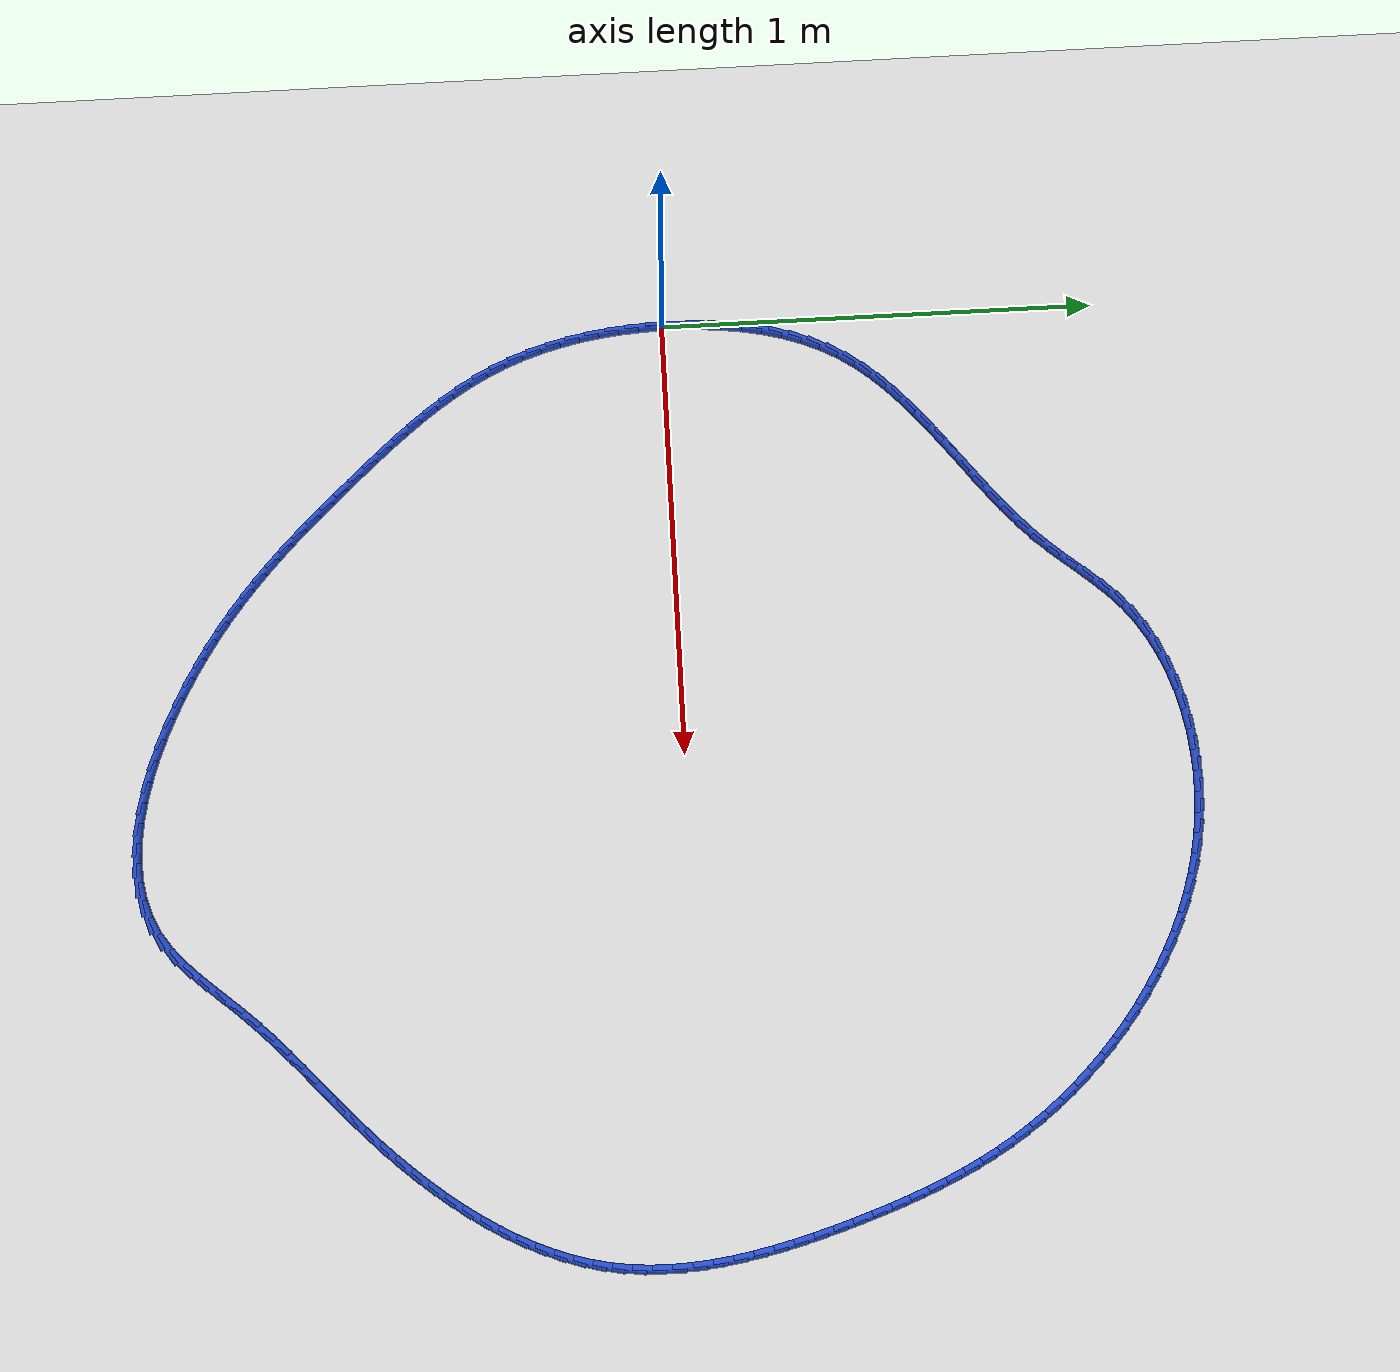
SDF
<sdf version="1.6">
 <world name="default">
  <light name="sun" type="directional">
   <pose>0 0 10 0 -0 0</pose>
   <diffuse>0.8 0.8 0.8 1</diffuse>
   <specular>0.2 0.2 0.2 1</specular>
   <attenuation>
    <range>1000</range>
    <constant>0.9</constant>
    <linear>0.01</linear>
    <quadratic>0.001</quadratic>
   </attenuation>
   <direction>-0.5 0.1 -0.9</direction>
  </light>
  <model name="ground_plane">
   <static>1</static>
   <link name="link">
    <collision name="collision">
     <geometry><plane><normal>0 0 1</normal><size>100 100</size></plane></geometry>
     <surface><friction><ode><mu>100</mu><mu2>50</mu2></ode></friction></surface>
    </collision>
    <visual name="visual">
     <cast_shadows>0</cast_shadows>
     <geometry><plane><normal>0 0 1</normal><size>100 100</size></plane></geometry>
     <material>
      <script><uri>file://media/materials/scripts/gazebo.material</uri><name>Gazebo/WhiteGlow</name></script>
     </material>
    </visual>
   </link>
  </model>
  <gravity>0 0 -9.8</gravity>
  <magnetic_field>6e-06 2.3e-05 -4.2e-05</magnetic_field>
  <atmosphere type="adiabatic"/>
  <physics name="default_physics" default="0" type="ode">
   <max_step_size>0.001</max_step_size>
   <real_time_factor>1</real_time_factor>
   <real_time_update_rate>1000</real_time_update_rate>
  </physics>
  <scene><ambient>0.4 0.4 0.4 1</ambient><background>0.7 0.7 0.7 1</background><shadows>1</shadows></scene>
  <spherical_coordinates>
   <surface_model>EARTH_WGS84</surface_model>
   <latitude_deg>0</latitude_deg>
   <longitude_deg>0</longitude_deg>
   <elevation>0</elevation>
   <heading_deg>0</heading_deg>
  </spherical_coordinates>
  <model name="line">
   <link name="link_0">
    <pose>3.2959746043559335e-17 1.3877787807814457e-16 0.01 0 1.57 1.5654988172962232</pose>
    <collision name="collision">
     <geometry><cylinder><radius>0.01</radius><length>0.08</length></cylinder></geometry>
    </collision>
    <visual name="visual">
     <material>
      <script><name>Gazebo/Blue</name><uri>file://media/materials/scripts/gazebo.material</uri></script>
     </material>
     <geometry><cylinder><radius>0.01</radius><length>0.08</length></cylinder></geometry>
    </visual>
   </link>
   <link name="link_1">
    <pose>0.0002555967554684817 0.04824802381930982 0.01 0 1.57 1.5253446536705428</pose>
    <collision name="collision">
     <geometry><cylinder><radius>0.01</radius><length>0.08</length></cylinder></geometry>
    </collision>
    <visual name="visual">
     <material>
      <script><name>Gazebo/Blue</name><uri>file://media/materials/scripts/gazebo.material</uri></script>
     </material>
     <geometry><cylinder><radius>0.01</radius><length>0.08</length></cylinder></geometry>
    </visual>
   </link>
   <link name="link_2">
    <pose>0.0024501504451312165 0.09649800277802285 0.01 0 1.57 1.4808697937102777</pose>
    <collision name="collision">
     <geometry><cylinder><radius>0.01</radius><length>0.08</length></cylinder></geometry>
    </collision>
    <visual name="visual">
     <material>
      <script><name>Gazebo/Blue</name><uri>file://media/materials/scripts/gazebo.material</uri></script>
     </material>
     <geometry><cylinder><radius>0.01</radius><length>0.08</length></cylinder></geometry>
    </visual>
   </link>
   <link name="link_3">
    <pose>0.006774525556622968 0.14445617391691548 0.01 0 1.57 1.431433383375195</pose>
    <collision name="collision">
     <geometry><cylinder><radius>0.01</radius><length>0.08</length></cylinder></geometry>
    </collision>
    <visual name="visual">
     <material>
      <script><name>Gazebo/Blue</name><uri>file://media/materials/scripts/gazebo.material</uri></script>
     </material>
     <geometry><cylinder><radius>0.01</radius><length>0.08</length></cylinder></geometry>
    </visual>
   </link>
   <link name="link_4">
    <pose>0.01341958657757848 0.19182877427676417 0.01 0 1.57 1.3763400883219323</pose>
    <collision name="collision">
     <geometry><cylinder><radius>0.01</radius><length>0.08</length></cylinder></geometry>
    </collision>
    <visual name="visual">
     <material>
      <script><name>Gazebo/Blue</name><uri>file://media/materials/scripts/gazebo.material</uri></script>
     </material>
     <geometry><cylinder><radius>0.01</radius><length>0.08</length></cylinder></geometry>
    </visual>
   </link>
   <link name="link_5">
    <pose>0.022576197995632485 0.23832204089834522 0.01 0 1.57 1.3148626369471914</pose>
    <collision name="collision">
     <geometry><cylinder><radius>0.01</radius><length>0.08</length></cylinder></geometry>
    </collision>
    <visual name="visual">
     <material>
      <script><name>Gazebo/Blue</name><uri>file://media/materials/scripts/gazebo.material</uri></script>
     </material>
     <geometry><cylinder><radius>0.01</radius><length>0.08</length></cylinder></geometry>
    </visual>
   </link>
   <link name="link_6">
    <pose>0.03443522429841973 0.2836422108224351 0.01 0 1.57 1.2462872489550638</pose>
    <collision name="collision">
     <geometry><cylinder><radius>0.01</radius><length>0.08</length></cylinder></geometry>
    </collision>
    <visual name="visual">
     <material>
      <script><name>Gazebo/Blue</name><uri>file://media/materials/scripts/gazebo.material</uri></script>
     </material>
     <geometry><cylinder><radius>0.01</radius><length>0.08</length></cylinder></geometry>
    </visual>
   </link>
   <link name="link_7">
    <pose>0.04918752997357492 0.32749552108980995 0.01 0 1.57 1.1699914999448833</pose>
    <collision name="collision">
     <geometry><cylinder><radius>0.01</radius><length>0.08</length></cylinder></geometry>
    </collision>
    <visual name="visual">
     <material>
      <script><name>Gazebo/Blue</name><uri>file://media/materials/scripts/gazebo.material</uri></script>
     </material>
     <geometry><cylinder><radius>0.01</radius><length>0.08</length></cylinder></geometry>
    </visual>
   </link>
   <link name="link_8">
    <pose>0.06702397950873284 0.3695882087412463 0.01 0 1.57 1.08556363328093</pose>
    <collision name="collision">
     <geometry><cylinder><radius>0.01</radius><length>0.08</length></cylinder></geometry>
    </collision>
    <visual name="visual">
     <material>
      <script><name>Gazebo/Blue</name><uri>file://media/materials/scripts/gazebo.material</uri></script>
     </material>
     <geometry><cylinder><radius>0.01</radius><length>0.08</length></cylinder></geometry>
    </visual>
   </link>
   <link name="link_9">
    <pose>0.08813539696439802 0.40962655066055487 0.01 0 1.57 0.9967152413968317</pose>
    <collision name="collision">
     <geometry><cylinder><radius>0.01</radius><length>0.08</length></cylinder></geometry>
    </collision>
    <visual name="visual">
     <material>
      <script><name>Gazebo/Blue</name><uri>file://media/materials/scripts/gazebo.material</uri></script>
     </material>
     <geometry><cylinder><radius>0.01</radius><length>0.08</length></cylinder></geometry>
    </visual>
   </link>
   <link name="link_10">
    <pose>0.11258963824109372 0.4474380152336753 0.01 0 1.57 0.9163013546582254</pose>
    <collision name="collision">
     <geometry><cylinder><radius>0.01</radius><length>0.08</length></cylinder></geometry>
    </collision>
    <visual name="visual">
     <material>
      <script><name>Gazebo/Blue</name><uri>file://media/materials/scripts/gazebo.material</uri></script>
     </material>
     <geometry><cylinder><radius>0.01</radius><length>0.08</length></cylinder></geometry>
    </visual>
   </link>
   <link name="link_11">
    <pose>0.14006025451220633 0.48323867861448977 0.01 0 1.57 0.8476876050398723</pose>
    <collision name="collision">
     <geometry><cylinder><radius>0.01</radius><length>0.08</length></cylinder></geometry>
    </collision>
    <visual name="visual">
     <material>
      <script><name>Gazebo/Blue</name><uri>file://media/materials/scripts/gazebo.material</uri></script>
     </material>
     <geometry><cylinder><radius>0.01</radius><length>0.08</length></cylinder></geometry>
    </visual>
   </link>
   <link name="link_12">
    <pose>0.17014192487456226 0.5173223494807773 0.01 0 1.57 0.7911424511987577</pose>
    <collision name="collision">
     <geometry><cylinder><radius>0.01</radius><length>0.08</length></cylinder></geometry>
    </collision>
    <visual name="visual">
     <material>
      <script><name>Gazebo/Blue</name><uri>file://media/materials/scripts/gazebo.material</uri></script>
     </material>
     <geometry><cylinder><radius>0.01</radius><length>0.08</length></cylinder></geometry>
    </visual>
   </link>
   <link name="link_13">
    <pose>0.20242932842498798 0.5499828365103169 0.01 0 1.57 0.7464549583323634</pose>
    <collision name="collision">
     <geometry><cylinder><radius>0.01</radius><length>0.08</length></cylinder></geometry>
    </collision>
    <visual name="visual">
     <material>
      <script><name>Gazebo/Blue</name><uri>file://media/materials/scripts/gazebo.material</uri></script>
     </material>
     <geometry><cylinder><radius>0.01</radius><length>0.08</length></cylinder></geometry>
    </visual>
   </link>
   <link name="link_14">
    <pose>0.23651714426030995 0.5815139483808873 0.01 0 1.57 0.7131837666676182</pose>
    <collision name="collision">
     <geometry><cylinder><radius>0.01</radius><length>0.08</length></cylinder></geometry>
    </collision>
    <visual name="visual">
     <material>
      <script><name>Gazebo/Blue</name><uri>file://media/materials/scripts/gazebo.material</uri></script>
     </material>
     <geometry><cylinder><radius>0.01</radius><length>0.08</length></cylinder></geometry>
    </visual>
   </link>
   <link name="link_15">
    <pose>0.2720000514773548 0.6122094937702682 0.01 0 1.57 0.6908404510857581</pose>
    <collision name="collision">
     <geometry><cylinder><radius>0.01</radius><length>0.08</length></cylinder></geometry>
    </collision>
    <visual name="visual">
     <material>
      <script><name>Gazebo/Blue</name><uri>file://media/materials/scripts/gazebo.material</uri></script>
     </material>
     <geometry><cylinder><radius>0.01</radius><length>0.08</length></cylinder></geometry>
    </visual>
   </link>
   <link name="link_16">
    <pose>0.3084727291729488 0.6423632813562383 0.01 0 1.57 0.6790067243754607</pose>
    <collision name="collision">
     <geometry><cylinder><radius>0.01</radius><length>0.08</length></cylinder></geometry>
    </collision>
    <visual name="visual">
     <material>
      <script><name>Gazebo/Blue</name><uri>file://media/materials/scripts/gazebo.material</uri></script>
     </material>
     <geometry><cylinder><radius>0.01</radius><length>0.08</length></cylinder></geometry>
    </visual>
   </link>
   <link name="link_17">
    <pose>0.34552985644391854 0.6722691198165763 0.01 0 1.57 0.6773994261593566</pose>
    <collision name="collision">
     <geometry><cylinder><radius>0.01</radius><length>0.08</length></cylinder></geometry>
    </collision>
    <visual name="visual">
     <material>
      <script><name>Gazebo/Blue</name><uri>file://media/materials/scripts/gazebo.material</uri></script>
     </material>
     <geometry><cylinder><radius>0.01</radius><length>0.08</length></cylinder></geometry>
    </visual>
   </link>
   <link name="link_18">
    <pose>0.38276611238709046 0.7022208178290616 0.01 0 1.57 0.6858978935743995</pose>
    <collision name="collision">
     <geometry><cylinder><radius>0.01</radius><length>0.08</length></cylinder></geometry>
    </collision>
    <visual name="visual">
     <material>
      <script><name>Gazebo/Blue</name><uri>file://media/materials/scripts/gazebo.material</uri></script>
     </material>
     <geometry><cylinder><radius>0.01</radius><length>0.08</length></cylinder></geometry>
    </visual>
   </link>
   <link name="link_19">
    <pose>0.41977617609929113 0.7325121840714734 0.01 0 1.57 0.7045431374903761</pose>
    <collision name="collision">
     <geometry><cylinder><radius>0.01</radius><length>0.08</length></cylinder></geometry>
    </collision>
    <visual name="visual">
     <material>
      <script><name>Gazebo/Blue</name><uri>file://media/materials/scripts/gazebo.material</uri></script>
     </material>
     <geometry><cylinder><radius>0.01</radius><length>0.08</length></cylinder></geometry>
    </visual>
   </link>
   <link name="link_20">
    <pose>0.4561547266773468 0.7634370272215902 0.01 0 1.57 0.7335116303648233</pose>
    <collision name="collision">
     <geometry><cylinder><radius>0.01</radius><length>0.08</length></cylinder></geometry>
    </collision>
    <visual name="visual">
     <material>
      <script><name>Gazebo/Blue</name><uri>file://media/materials/scripts/gazebo.material</uri></script>
     </material>
     <geometry><cylinder><radius>0.01</radius><length>0.08</length></cylinder></geometry>
    </visual>
   </link>
   <link name="link_21">
    <pose>0.4914964432180841 0.7952891559571913 0.01 0 1.57 0.773060365631753</pose>
    <collision name="collision">
     <geometry><cylinder><radius>0.01</radius><length>0.08</length></cylinder></geometry>
    </collision>
    <visual name="visual">
     <material>
      <script><name>Gazebo/Blue</name><uri>file://media/materials/scripts/gazebo.material</uri></script>
     </material>
     <geometry><cylinder><radius>0.01</radius><length>0.08</length></cylinder></geometry>
    </visual>
   </link>
   <link name="link_22">
    <pose>0.5253960048183295 0.8283623789560559 0.01 0 1.57 0.8234040705962363</pose>
    <collision name="collision">
     <geometry><cylinder><radius>0.01</radius><length>0.08</length></cylinder></geometry>
    </collision>
    <visual name="visual">
     <material>
      <script><name>Gazebo/Blue</name><uri>file://media/materials/scripts/gazebo.material</uri></script>
     </material>
     <geometry><cylinder><radius>0.01</radius><length>0.08</length></cylinder></geometry>
    </visual>
   </link>
   <link name="link_23">
    <pose>0.5574492022800209 0.8629495232312983 0.01 0 1.57 0.873608936489605</pose>
    <collision name="collision">
     <geometry><cylinder><radius>0.01</radius><length>0.08</length></cylinder></geometry>
    </collision>
    <visual name="visual">
     <material>
      <script><name>Gazebo/Blue</name><uri>file://media/materials/scripts/gazebo.material</uri></script>
     </material>
     <geometry><cylinder><radius>0.01</radius><length>0.08</length></cylinder></geometry>
    </visual>
   </link>
   <link name="link_24">
    <pose>0.5876409893200333 0.8989997747724332 0.01 0 1.57 0.8963443819122033</pose>
    <collision name="collision">
     <geometry><cylinder><radius>0.01</radius><length>0.08</length></cylinder></geometry>
    </collision>
    <visual name="visual">
     <material>
      <script><name>Gazebo/Blue</name><uri>file://media/materials/scripts/gazebo.material</uri></script>
     </material>
     <geometry><cylinder><radius>0.01</radius><length>0.08</length></cylinder></geometry>
    </visual>
   </link>
   <link name="link_25">
    <pose>0.6169158458185611 0.9356150328921682 0.01 0 1.57 0.8872708833737211</pose>
    <collision name="collision">
     <geometry><cylinder><radius>0.01</radius><length>0.08</length></cylinder></geometry>
    </collision>
    <visual name="visual">
     <material>
      <script><name>Gazebo/Blue</name><uri>file://media/materials/scripts/gazebo.material</uri></script>
     </material>
     <geometry><cylinder><radius>0.01</radius><length>0.08</length></cylinder></geometry>
    </visual>
   </link>
   <link name="link_26">
    <pose>0.6463635143198141 0.9717689261748429 0.01 0 1.57 0.845834614131423</pose>
    <collision name="collision">
     <geometry><cylinder><radius>0.01</radius><length>0.08</length></cylinder></geometry>
    </collision>
    <visual name="visual">
     <material>
      <script><name>Gazebo/Blue</name><uri>file://media/materials/scripts/gazebo.material</uri></script>
     </material>
     <geometry><cylinder><radius>0.01</radius><length>0.08</length></cylinder></geometry>
    </visual>
   </link>
   <link name="link_27">
    <pose>0.6770737373680019 1.006435083204797 0.01 0 1.57 0.7714594543512581</pose>
    <collision name="collision">
     <geometry><cylinder><radius>0.01</radius><length>0.08</length></cylinder></geometry>
    </collision>
    <visual name="visual">
     <material>
      <script><name>Gazebo/Blue</name><uri>file://media/materials/scripts/gazebo.material</uri></script>
     </material>
     <geometry><cylinder><radius>0.01</radius><length>0.08</length></cylinder></geometry>
    </visual>
   </link>
   <link name="link_28">
    <pose>0.7101354433165653 1.0385877264404748 0.01 0 1.57 0.6742653255553979</pose>
    <collision name="collision">
     <geometry><cylinder><radius>0.01</radius><length>0.08</length></cylinder></geometry>
    </collision>
    <visual name="visual">
     <material>
      <script><name>Gazebo/Blue</name><uri>file://media/materials/scripts/gazebo.material</uri></script>
     </material>
     <geometry><cylinder><radius>0.01</radius><length>0.08</length></cylinder></geometry>
    </visual>
   </link>
   <link name="link_29">
    <pose>0.7462712961701522 1.0674682330670155 0.01 0 1.57 0.5798626314763252</pose>
    <collision name="collision">
     <geometry><cylinder><radius>0.01</radius><length>0.08</length></cylinder></geometry>
    </collision>
    <visual name="visual">
     <material>
      <script><name>Gazebo/Blue</name><uri>file://media/materials/scripts/gazebo.material</uri></script>
     </material>
     <geometry><cylinder><radius>0.01</radius><length>0.08</length></cylinder></geometry>
    </visual>
   </link>
   <link name="link_30">
    <pose>0.7852612720232829 1.0930055807193944 0.01 0 1.57 0.492067666545524</pose>
    <collision name="collision">
     <geometry><cylinder><radius>0.01</radius><length>0.08</length></cylinder></geometry>
    </collision>
    <visual name="visual">
     <material>
      <script><name>Gazebo/Blue</name><uri>file://media/materials/scripts/gazebo.material</uri></script>
     </material>
     <geometry><cylinder><radius>0.01</radius><length>0.08</length></cylinder></geometry>
    </visual>
   </link>
   <link name="link_31">
    <pose>0.8267357604268825 1.1152378560744651 0.01 0 1.57 0.41038548225211213</pose>
    <collision name="collision">
     <geometry><cylinder><radius>0.01</radius><length>0.08</length></cylinder></geometry>
    </collision>
    <visual name="visual">
     <material>
      <script><name>Gazebo/Blue</name><uri>file://media/materials/scripts/gazebo.material</uri></script>
     </material>
     <geometry><cylinder><radius>0.01</radius><length>0.08</length></cylinder></geometry>
    </visual>
   </link>
   <link name="link_32">
    <pose>0.8703251509318759 1.1342031458090827 0.01 0 1.57 0.33410319359552026</pose>
    <collision name="collision">
     <geometry><cylinder><radius>0.01</radius><length>0.08</length></cylinder></geometry>
    </collision>
    <visual name="visual">
     <material>
      <script><name>Gazebo/Blue</name><uri>file://media/materials/scripts/gazebo.material</uri></script>
     </material>
     <geometry><cylinder><radius>0.01</radius><length>0.08</length></cylinder></geometry>
    </visual>
   </link>
   <link name="link_33">
    <pose>0.9156598330891887 1.1499395366001002 0.01 0 1.57 0.2623900255819134</pose>
    <collision name="collision">
     <geometry><cylinder><radius>0.01</radius><length>0.08</length></cylinder></geometry>
    </collision>
    <visual name="visual">
     <material>
      <script><name>Gazebo/Blue</name><uri>file://media/materials/scripts/gazebo.material</uri></script>
     </material>
     <geometry><cylinder><radius>0.01</radius><length>0.08</length></cylinder></geometry>
    </visual>
   </link>
   <link name="link_34">
    <pose>0.9623701964497462 1.1624851151243727 0.01 0 1.57 0.1943623223673569</pose>
    <collision name="collision">
     <geometry><cylinder><radius>0.01</radius><length>0.08</length></cylinder></geometry>
    </collision>
    <visual name="visual">
     <material>
      <script><name>Gazebo/Blue</name><uri>file://media/materials/scripts/gazebo.material</uri></script>
     </material>
     <geometry><cylinder><radius>0.01</radius><length>0.08</length></cylinder></geometry>
    </visual>
   </link>
   <link name="link_35">
    <pose>1.0100866305644736 1.1718779680587539 0.01 0 1.57 0.12911916920360797</pose>
    <collision name="collision">
     <geometry><cylinder><radius>0.01</radius><length>0.08</length></cylinder></geometry>
    </collision>
    <visual name="visual">
     <material>
      <script><name>Gazebo/Blue</name><uri>file://media/materials/scripts/gazebo.material</uri></script>
     </material>
     <geometry><cylinder><radius>0.01</radius><length>0.08</length></cylinder></geometry>
    </visual>
   </link>
   <link name="link_36">
    <pose>1.0584395249842964 1.1781561820800983 0.01 0 1.57 0.06575612400365066</pose>
    <collision name="collision">
     <geometry><cylinder><radius>0.01</radius><length>0.08</length></cylinder></geometry>
    </collision>
    <visual name="visual">
     <material>
      <script><name>Gazebo/Blue</name><uri>file://media/materials/scripts/gazebo.material</uri></script>
     </material>
     <geometry><cylinder><radius>0.01</radius><length>0.08</length></cylinder></geometry>
    </visual>
   </link>
   <link name="link_37">
    <pose>1.1070592692601389 1.1813578438652597 0.01 0 1.57 0.003363680055081965</pose>
    <collision name="collision">
     <geometry><cylinder><radius>0.01</radius><length>0.08</length></cylinder></geometry>
    </collision>
    <visual name="visual">
     <material>
      <script><name>Gazebo/Blue</name><uri>file://media/materials/scripts/gazebo.material</uri></script>
     </material>
     <geometry><cylinder><radius>0.01</radius><length>0.08</length></cylinder></geometry>
    </visual>
   </link>
   <link name="link_38">
    <pose>1.1555762529429277 1.1815210400910927 0.01 0 1.57 -0.05898399173584973</pose>
    <collision name="collision">
     <geometry><cylinder><radius>0.01</radius><length>0.08</length></cylinder></geometry>
    </collision>
    <visual name="visual">
     <material>
      <script><name>Gazebo/Blue</name><uri>file://media/materials/scripts/gazebo.material</uri></script>
     </material>
     <geometry><cylinder><radius>0.01</radius><length>0.08</length></cylinder></geometry>
    </visual>
   </link>
   <link name="link_39">
    <pose>1.2036209507515252 1.178683881005139 0.01 0 1.57 -0.12158685568217643</pose>
    <collision name="collision">
     <geometry><cylinder><radius>0.01</radius><length>0.08</length></cylinder></geometry>
    </collision>
    <visual name="visual">
     <material>
      <script><name>Gazebo/Blue</name><uri>file://media/materials/scripts/gazebo.material</uri></script>
     </material>
     <geometry><cylinder><radius>0.01</radius><length>0.08</length></cylinder></geometry>
    </visual>
   </link>
   <link name="link_40">
    <pose>1.2509033058232113 1.172906470169706 0.01 0 1.57 -0.18293787763764124</pose>
    <collision name="collision">
     <geometry><cylinder><radius>0.01</radius><length>0.08</length></cylinder></geometry>
    </collision>
    <visual name="visual">
     <material>
      <script><name>Gazebo/Blue</name><uri>file://media/materials/scripts/gazebo.material</uri></script>
     </material>
     <geometry><cylinder><radius>0.01</radius><length>0.08</length></cylinder></geometry>
    </visual>
   </link>
   <link name="link_41">
    <pose>1.2973600558809046 1.164311677775767 0.01 0 1.57 -0.2424214555079705</pose>
    <collision name="collision">
     <geometry><cylinder><radius>0.01</radius><length>0.08</length></cylinder></geometry>
    </collision>
    <visual name="visual">
     <material>
      <script><name>Gazebo/Blue</name><uri>file://media/materials/scripts/gazebo.material</uri></script>
     </material>
     <geometry><cylinder><radius>0.01</radius><length>0.08</length></cylinder></geometry>
    </visual>
   </link>
   <link name="link_42">
    <pose>1.3429681334409307 1.1530334981408448 0.01 0 1.57 -0.2997756070706618</pose>
    <collision name="collision">
     <geometry><cylinder><radius>0.01</radius><length>0.08</length></cylinder></geometry>
    </collision>
    <visual name="visual">
     <material>
      <script><name>Gazebo/Blue</name><uri>file://media/materials/scripts/gazebo.material</uri></script>
     </material>
     <geometry><cylinder><radius>0.01</radius><length>0.08</length></cylinder></geometry>
    </visual>
   </link>
   <link name="link_43">
    <pose>1.387704471019614 1.1392059255824643 0.01 0 1.57 -0.35481330731606464</pose>
    <collision name="collision">
     <geometry><cylinder><radius>0.01</radius><length>0.08</length></cylinder></geometry>
    </collision>
    <visual name="visual">
     <material>
      <script><name>Gazebo/Blue</name><uri>file://media/materials/scripts/gazebo.material</uri></script>
     </material>
     <geometry><cylinder><radius>0.01</radius><length>0.08</length></cylinder></geometry>
    </visual>
   </link>
   <link name="link_44">
    <pose>1.431546001133279 1.1229629544181488 0.01 0 1.57 -0.4074186484710152</pose>
    <collision name="collision">
     <geometry><cylinder><radius>0.01</radius><length>0.08</length></cylinder></geometry>
    </collision>
    <visual name="visual">
     <material>
      <script><name>Gazebo/Blue</name><uri>file://media/materials/scripts/gazebo.material</uri></script>
     </material>
     <geometry><cylinder><radius>0.01</radius><length>0.08</length></cylinder></geometry>
    </visual>
   </link>
   <link name="link_45">
    <pose>1.4744696562982509 1.1044385789654223 0.01 0 1.57 -0.4575395148401608</pose>
    <collision name="collision">
     <geometry><cylinder><radius>0.01</radius><length>0.08</length></cylinder></geometry>
    </collision>
    <visual name="visual">
     <material>
      <script><name>Gazebo/Blue</name><uri>file://media/materials/scripts/gazebo.material</uri></script>
     </material>
     <geometry><cylinder><radius>0.01</radius><length>0.08</length></cylinder></geometry>
    </visual>
   </link>
   <link name="link_46">
    <pose>1.5164523690308542 1.0837667935418096 0.01 0 1.57 -0.5051782513102805</pose>
    <collision name="collision">
     <geometry><cylinder><radius>0.01</radius><length>0.08</length></cylinder></geometry>
    </collision>
    <visual name="visual">
     <material>
      <script><name>Gazebo/Blue</name><uri>file://media/materials/scripts/gazebo.material</uri></script>
     </material>
     <geometry><cylinder><radius>0.01</radius><length>0.08</length></cylinder></geometry>
    </visual>
   </link>
   <link name="link_47">
    <pose>1.5574710718474134 1.0610815924648334 0.01 0 1.57 -0.5504797892830455</pose>
    <collision name="collision">
     <geometry><cylinder><radius>0.01</radius><length>0.08</length></cylinder></geometry>
    </collision>
    <visual name="visual">
     <material>
      <script><name>Gazebo/Blue</name><uri>file://media/materials/scripts/gazebo.material</uri></script>
     </material>
     <geometry><cylinder><radius>0.01</radius><length>0.08</length></cylinder></geometry>
    </visual>
   </link>
   <link name="link_48">
    <pose>1.5974990407556275 1.0365138041645316 0.01 0 1.57 -0.594469066658529</pose>
    <collision name="collision">
     <geometry><cylinder><radius>0.01</radius><length>0.08</length></cylinder></geometry>
    </collision>
    <visual name="visual">
     <material>
      <script><name>Gazebo/Blue</name><uri>file://media/materials/scripts/gazebo.material</uri></script>
     </material>
     <geometry><cylinder><radius>0.01</radius><length>0.08</length></cylinder></geometry>
    </visual>
   </link>
   <link name="link_49">
    <pose>1.6364749064457478 1.0101642603751275 0.01 0 1.57 -0.6378038408432082</pose>
    <collision name="collision">
     <geometry><cylinder><radius>0.01</radius><length>0.08</length></cylinder></geometry>
    </collision>
    <visual name="visual">
     <material>
      <script><name>Gazebo/Blue</name><uri>file://media/materials/scripts/gazebo.material</uri></script>
     </material>
     <geometry><cylinder><radius>0.01</radius><length>0.08</length></cylinder></geometry>
    </visual>
   </link>
   <link name="link_50">
    <pose>1.6743181905421396 0.9821172477713983 0.01 0 1.57 -0.6806447606829928</pose>
    <collision name="collision">
     <geometry><cylinder><radius>0.01</radius><length>0.08</length></cylinder></geometry>
    </collision>
    <visual name="visual">
     <material>
      <script><name>Gazebo/Blue</name><uri>file://media/materials/scripts/gazebo.material</uri></script>
     </material>
     <geometry><cylinder><radius>0.01</radius><length>0.08</length></cylinder></geometry>
    </visual>
   </link>
   <link name="link_51">
    <pose>1.7109482146159747 0.9524568798175655 0.01 0 1.57 -0.7231497540762527</pose>
    <collision name="collision">
     <geometry><cylinder><radius>0.01</radius><length>0.08</length></cylinder></geometry>
    </collision>
    <visual name="visual">
     <material>
      <script><name>Gazebo/Blue</name><uri>file://media/materials/scripts/gazebo.material</uri></script>
     </material>
     <geometry><cylinder><radius>0.01</radius><length>0.08</length></cylinder></geometry>
    </visual>
   </link>
   <link name="link_52">
    <pose>1.7462843002384274 0.9212672699778505 0.01 0 1.57 -0.7654787856757127</pose>
    <collision name="collision">
     <geometry><cylinder><radius>0.01</radius><length>0.08</length></cylinder></geometry>
    </collision>
    <visual name="visual">
     <material>
      <script><name>Gazebo/Blue</name><uri>file://media/materials/scripts/gazebo.material</uri></script>
     </material>
     <geometry><cylinder><radius>0.01</radius><length>0.08</length></cylinder></geometry>
    </visual>
   </link>
   <link name="link_53">
    <pose>1.780245768980671 0.8886325317164736 0.01 0 1.57 -0.8077934656024712</pose>
    <collision name="collision">
     <geometry><cylinder><radius>0.01</radius><length>0.08</length></cylinder></geometry>
    </collision>
    <visual name="visual">
     <material>
      <script><name>Gazebo/Blue</name><uri>file://media/materials/scripts/gazebo.material</uri></script>
     </material>
     <geometry><cylinder><radius>0.01</radius><length>0.08</length></cylinder></geometry>
    </visual>
   </link>
   <link name="link_54">
    <pose>1.812751942413878 0.8546367784976552 0.01 0 1.57 -0.8502567870368065</pose>
    <collision name="collision">
     <geometry><cylinder><radius>0.01</radius><length>0.08</length></cylinder></geometry>
    </collision>
    <visual name="visual">
     <material>
      <script><name>Gazebo/Blue</name><uri>file://media/materials/scripts/gazebo.material</uri></script>
     </material>
     <geometry><cylinder><radius>0.01</radius><length>0.08</length></cylinder></geometry>
    </visual>
   </link>
   <link name="link_55">
    <pose>1.8437221421092214 0.8193641237856172 0.01 0 1.57 -0.8930328994932771</pose>
    <collision name="collision">
     <geometry><cylinder><radius>0.01</radius><length>0.08</length></cylinder></geometry>
    </collision>
    <visual name="visual">
     <material>
      <script><name>Gazebo/Blue</name><uri>file://media/materials/scripts/gazebo.material</uri></script>
     </material>
     <geometry><cylinder><radius>0.01</radius><length>0.08</length></cylinder></geometry>
    </visual>
   </link>
   <link name="link_56">
    <pose>1.873075689637875 0.78289868104458 0.01 0 1.57 -0.9362868223097333</pose>
    <collision name="collision">
     <geometry><cylinder><radius>0.01</radius><length>0.08</length></cylinder></geometry>
    </collision>
    <visual name="visual">
     <material>
      <script><name>Gazebo/Blue</name><uri>file://media/materials/scripts/gazebo.material</uri></script>
     </material>
     <geometry><cylinder><radius>0.01</radius><length>0.08</length></cylinder></geometry>
    </visual>
   </link>
   <link name="link_57">
    <pose>1.900731906571012 0.7453245637387648 0.01 0 1.57 -0.980155334895303</pose>
    <collision name="collision">
     <geometry><cylinder><radius>0.01</radius><length>0.08</length></cylinder></geometry>
    </collision>
    <visual name="visual">
     <material>
      <script><name>Gazebo/Blue</name><uri>file://media/materials/scripts/gazebo.material</uri></script>
     </material>
     <geometry><cylinder><radius>0.01</radius><length>0.08</length></cylinder></geometry>
    </visual>
   </link>
   <link name="link_58">
    <pose>1.9266118898378368 0.7067256292664923 0.01 0 1.57 -1.0233508540933316</pose>
    <collision name="collision">
     <geometry><cylinder><radius>0.01</radius><length>0.08</length></cylinder></geometry>
    </collision>
    <visual name="visual">
     <material>
      <script><name>Gazebo/Blue</name><uri>file://media/materials/scripts/gazebo.material</uri></script>
     </material>
     <geometry><cylinder><radius>0.01</radius><length>0.08</length></cylinder></geometry>
    </visual>
   </link>
   <link name="link_59">
    <pose>1.9507228171243516 0.6671733193071 0.01 0 1.57 -1.063724761281476</pose>
    <collision name="collision">
     <geometry><cylinder><radius>0.01</radius><length>0.08</length></cylinder></geometry>
    </collision>
    <visual name="visual">
     <material>
      <script><name>Gazebo/Blue</name><uri>file://media/materials/scripts/gazebo.material</uri></script>
     </material>
     <geometry><cylinder><radius>0.01</radius><length>0.08</length></cylinder></geometry>
    </visual>
   </link>
   <link name="link_60">
    <pose>1.9731947026909686 0.6267213584049264 0.01 0 1.57 -1.1009181930275793</pose>
    <collision name="collision">
     <geometry><cylinder><radius>0.01</radius><length>0.08</length></cylinder></geometry>
    </collision>
    <visual name="visual">
     <material>
      <script><name>Gazebo/Blue</name><uri>file://media/materials/scripts/gazebo.material</uri></script>
     </material>
     <geometry><cylinder><radius>0.01</radius><length>0.08</length></cylinder></geometry>
    </visual>
   </link>
   <link name="link_61">
    <pose>1.9941669799121624 0.5854221125535995 0.01 0 1.57 -1.1347905037578787</pose>
    <collision name="collision">
     <geometry><cylinder><radius>0.01</radius><length>0.08</length></cylinder></geometry>
    </collision>
    <visual name="visual">
     <material>
      <script><name>Gazebo/Blue</name><uri>file://media/materials/scripts/gazebo.material</uri></script>
     </material>
     <geometry><cylinder><radius>0.01</radius><length>0.08</length></cylinder></geometry>
    </visual>
   </link>
   <link name="link_62">
    <pose>2.0137790821624075 0.5433279477467475 0.01 0 1.57 -1.165258480955744</pose>
    <collision name="collision">
     <geometry><cylinder><radius>0.01</radius><length>0.08</length></cylinder></geometry>
    </collision>
    <visual name="visual">
     <material>
      <script><name>Gazebo/Blue</name><uri>file://media/materials/scripts/gazebo.material</uri></script>
     </material>
     <geometry><cylinder><radius>0.01</radius><length>0.08</length></cylinder></geometry>
    </visual>
   </link>
   <link name="link_63">
    <pose>2.032170442816179 0.5004912299779996 0.01 0 1.57 -1.1922861336543689</pose>
    <collision name="collision">
     <geometry><cylinder><radius>0.01</radius><length>0.08</length></cylinder></geometry>
    </collision>
    <visual name="visual">
     <material>
      <script><name>Gazebo/Blue</name><uri>file://media/materials/scripts/gazebo.material</uri></script>
     </material>
     <geometry><cylinder><radius>0.01</radius><length>0.08</length></cylinder></geometry>
    </visual>
   </link>
   <link name="link_64">
    <pose>2.049480495247952 0.4569643252409837 0.01 0 1.57 -1.2158742222389296</pose>
    <collision name="collision">
     <geometry><cylinder><radius>0.01</radius><length>0.08</length></cylinder></geometry>
    </collision>
    <visual name="visual">
     <material>
      <script><name>Gazebo/Blue</name><uri>file://media/materials/scripts/gazebo.material</uri></script>
     </material>
     <geometry><cylinder><radius>0.01</radius><length>0.08</length></cylinder></geometry>
    </visual>
   </link>
   <link name="link_65">
    <pose>2.065848672832199 0.412799599529328 0.01 0 1.57 -1.236050401943354</pose>
    <collision name="collision">
     <geometry><cylinder><radius>0.01</radius><length>0.08</length></cylinder></geometry>
    </collision>
    <visual name="visual">
     <material>
      <script><name>Gazebo/Blue</name><uri>file://media/materials/scripts/gazebo.material</uri></script>
     </material>
     <geometry><cylinder><radius>0.01</radius><length>0.08</length></cylinder></geometry>
    </visual>
   </link>
   <link name="link_66">
    <pose>2.0814144089433975 0.3680494188366612 0.01 0 1.57 -1.252883592524103</pose>
    <collision name="collision">
     <geometry><cylinder><radius>0.01</radius><length>0.08</length></cylinder></geometry>
    </collision>
    <visual name="visual">
     <material>
      <script><name>Gazebo/Blue</name><uri>file://media/materials/scripts/gazebo.material</uri></script>
     </material>
     <geometry><cylinder><radius>0.01</radius><length>0.08</length></cylinder></geometry>
    </visual>
   </link>
   <link name="link_67">
    <pose>2.0963159416422736 0.3227662626731727 0.01 0 1.57 -1.2686904485807189</pose>
    <collision name="collision">
     <geometry><cylinder><radius>0.01</radius><length>0.08</length></cylinder></geometry>
    </collision>
    <visual name="visual">
     <material>
      <script><name>Gazebo/Blue</name><uri>file://media/materials/scripts/gazebo.material</uri></script>
     </material>
     <geometry><cylinder><radius>0.01</radius><length>0.08</length></cylinder></geometry>
    </visual>
   </link>
   <link name="link_68">
    <pose>2.1105744985434587 0.2770137227976692 0.01 0 1.57 -1.2876784618126416</pose>
    <collision name="collision">
     <geometry><cylinder><radius>0.01</radius><length>0.08</length></cylinder></geometry>
    </collision>
    <visual name="visual">
     <material>
      <script><name>Gazebo/Blue</name><uri>file://media/materials/scripts/gazebo.material</uri></script>
     </material>
     <geometry><cylinder><radius>0.01</radius><length>0.08</length></cylinder></geometry>
    </visual>
   </link>
   <link name="link_69">
    <pose>2.123997577090241 0.23087568849691065 0.01 0 1.57 -1.3104150665724807</pose>
    <collision name="collision">
     <geometry><cylinder><radius>0.01</radius><length>0.08</length></cylinder></geometry>
    </collision>
    <visual name="visual">
     <material>
      <script><name>Gazebo/Blue</name><uri>file://media/materials/scripts/gazebo.material</uri></script>
     </material>
     <geometry><cylinder><radius>0.01</radius><length>0.08</length></cylinder></geometry>
    </visual>
   </link>
   <link name="link_70">
    <pose>2.136369905959389 0.18443821136198688 0.01 0 1.57 -1.3370742787127068</pose>
    <collision name="collision">
     <geometry><cylinder><radius>0.01</radius><length>0.08</length></cylinder></geometry>
    </collision>
    <visual name="visual">
     <material>
      <script><name>Gazebo/Blue</name><uri>file://media/materials/scripts/gazebo.material</uri></script>
     </material>
     <geometry><cylinder><radius>0.01</radius><length>0.08</length></cylinder></geometry>
    </visual>
   </link>
   <link name="link_71">
    <pose>2.1474762138276717 0.1377873429839879 0.01 0 1.57 -1.3678698956714423</pose>
    <collision name="collision">
     <geometry><cylinder><radius>0.01</radius><length>0.08</length></cylinder></geometry>
    </collision>
    <visual name="visual">
     <material>
      <script><name>Gazebo/Blue</name><uri>file://media/materials/scripts/gazebo.material</uri></script>
     </material>
     <geometry><cylinder><radius>0.01</radius><length>0.08</length></cylinder></geometry>
    </visual>
   </link>
   <link name="link_72">
    <pose>2.157101229371857 0.0910091349540044 0.01 0 1.57 -1.4030469033667108</pose>
    <collision name="collision">
     <geometry><cylinder><radius>0.01</radius><length>0.08</length></cylinder></geometry>
    </collision>
    <visual name="visual">
     <material>
      <script><name>Gazebo/Blue</name><uri>file://media/materials/scripts/gazebo.material</uri></script>
     </material>
     <geometry><cylinder><radius>0.01</radius><length>0.08</length></cylinder></geometry>
    </visual>
   </link>
   <link name="link_73">
    <pose>2.1650296812687144 0.0441896388631262 0.01 0 1.57 -1.4428691456185951</pose>
    <collision name="collision">
     <geometry><cylinder><radius>0.01</radius><length>0.08</length></cylinder></geometry>
    </collision>
    <visual name="visual">
     <material>
      <script><name>Gazebo/Blue</name><uri>file://media/materials/scripts/gazebo.material</uri></script>
     </material>
     <geometry><cylinder><radius>0.01</radius><length>0.08</length></cylinder></geometry>
    </visual>
   </link>
   <link name="link_74">
    <pose>2.171046298195012 -0.002585093697556568 0.01 0 1.57 -1.487601494364988</pose>
    <collision name="collision">
     <geometry><cylinder><radius>0.01</radius><length>0.08</length></cylinder></geometry>
    </collision>
    <visual name="visual">
     <material>
      <script><name>Gazebo/Blue</name><uri>file://media/materials/scripts/gazebo.material</uri></script>
     </material>
     <geometry><cylinder><radius>0.01</radius><length>0.08</length></cylinder></geometry>
    </visual>
   </link>
   <link name="link_75">
    <pose>2.174935808827518 -0.04922901113695382 0.01 0 1.57 -1.5374846974181913</pose>
    <collision name="collision">
     <geometry><cylinder><radius>0.01</radius><length>0.08</length></cylinder></geometry>
    </collision>
    <visual name="visual">
     <material>
      <script><name>Gazebo/Blue</name><uri>file://media/materials/scripts/gazebo.material</uri></script>
     </material>
     <geometry><cylinder><radius>0.01</radius><length>0.08</length></cylinder></geometry>
    </visual>
   </link>
   <link name="link_76">
    <pose>2.1764829418430023 -0.09565606186397577 0.01 0 1.57 1.5488912146573024</pose>
    <collision name="collision">
     <geometry><cylinder><radius>0.01</radius><length>0.08</length></cylinder></geometry>
    </collision>
    <visual name="visual">
     <material>
      <script><name>Gazebo/Blue</name><uri>file://media/materials/scripts/gazebo.material</uri></script>
     </material>
     <geometry><cylinder><radius>0.01</radius><length>0.08</length></cylinder></geometry>
    </visual>
   </link>
   <link name="link_77">
    <pose>2.1754724259182328 -0.141780194287532 0.01 0 1.57 1.4882593746283577</pose>
    <collision name="collision">
     <geometry><cylinder><radius>0.01</radius><length>0.08</length></cylinder></geometry>
    </collision>
    <visual name="visual">
     <material>
      <script><name>Gazebo/Blue</name><uri>file://media/materials/scripts/gazebo.material</uri></script>
     </material>
     <geometry><cylinder><radius>0.01</radius><length>0.08</length></cylinder></geometry>
    </visual>
   </link>
   <link name="link_78">
    <pose>2.171688989729978 -0.1875153568165316 0.01 0 1.57 1.4222822419189516</pose>
    <collision name="collision">
     <geometry><cylinder><radius>0.01</radius><length>0.08</length></cylinder></geometry>
    </collision>
    <visual name="visual">
     <material>
      <script><name>Gazebo/Blue</name><uri>file://media/materials/scripts/gazebo.material</uri></script>
     </material>
     <geometry><cylinder><radius>0.01</radius><length>0.08</length></cylinder></geometry>
    </visual>
   </link>
   <link name="link_79">
    <pose>2.1649173619550064 -0.23277549785988588 0.01 0 1.57 1.3518458025767466</pose>
    <collision name="collision">
     <geometry><cylinder><radius>0.01</radius><length>0.08</length></cylinder></geometry>
    </collision>
    <visual name="visual">
     <material>
      <script><name>Gazebo/Blue</name><uri>file://media/materials/scripts/gazebo.material</uri></script>
     </material>
     <geometry><cylinder><radius>0.01</radius><length>0.08</length></cylinder></geometry>
    </visual>
   </link>
   <link name="link_80">
    <pose>2.1549704671714847 -0.27747708206271465 0.01 0 1.57 1.2829829458439481</pose>
    <collision name="collision">
     <geometry><cylinder><radius>0.01</radius><length>0.08</length></cylinder></geometry>
    </collision>
    <visual name="visual">
     <material>
      <script><name>Gazebo/Blue</name><uri>file://media/materials/scripts/gazebo.material</uri></script>
     </material>
     <geometry><cylinder><radius>0.01</radius><length>0.08</length></cylinder></geometry>
    </visual>
   </link>
   <link name="link_81">
    <pose>2.141920552794768 -0.3215597163525657 0.01 0 1.57 1.2189066348545567</pose>
    <collision name="collision">
     <geometry><cylinder><radius>0.01</radius><length>0.08</length></cylinder></geometry>
    </collision>
    <visual name="visual">
     <material>
      <script><name>Gazebo/Blue</name><uri>file://media/materials/scripts/gazebo.material</uri></script>
     </material>
     <geometry><cylinder><radius>0.01</radius><length>0.08</length></cylinder></geometry>
    </visual>
   </link>
   <link name="link_82">
    <pose>2.1259795266835018 -0.3649754711232077 0.01 0 1.57 1.1596216933000074</pose>
    <collision name="collision">
     <geometry><cylinder><radius>0.01</radius><length>0.08</length></cylinder></geometry>
    </collision>
    <visual name="visual">
     <material>
      <script><name>Gazebo/Blue</name><uri>file://media/materials/scripts/gazebo.material</uri></script>
     </material>
     <geometry><cylinder><radius>0.01</radius><length>0.08</length></cylinder></geometry>
    </visual>
   </link>
   <link name="link_83">
    <pose>2.1073606471879227 -0.4076765372879063 0.01 0 1.57 1.1049728517843413</pose>
    <collision name="collision">
     <geometry><cylinder><radius>0.01</radius><length>0.08</length></cylinder></geometry>
    </collision>
    <visual name="visual">
     <material>
      <script><name>Gazebo/Blue</name><uri>file://media/materials/scripts/gazebo.material</uri></script>
     </material>
     <geometry><cylinder><radius>0.01</radius><length>0.08</length></cylinder></geometry>
    </visual>
   </link>
   <link name="link_84">
    <pose>2.08627717265827 -0.44961510575992936 0.01 0 1.57 1.0547175023799293</pose>
    <collision name="collision">
     <geometry><cylinder><radius>0.01</radius><length>0.08</length></cylinder></geometry>
    </collision>
    <visual name="visual">
     <material>
      <script><name>Gazebo/Blue</name><uri>file://media/materials/scripts/gazebo.material</uri></script>
     </material>
     <geometry><cylinder><radius>0.01</radius><length>0.08</length></cylinder></geometry>
    </visual>
   </link>
   <link name="link_85">
    <pose>2.062942361444781 -0.49074336745254166 0.01 0 1.57 1.0085616285222379</pose>
    <collision name="collision">
     <geometry><cylinder><radius>0.01</radius><length>0.08</length></cylinder></geometry>
    </collision>
    <visual name="visual">
     <material>
      <script><name>Gazebo/Blue</name><uri>file://media/materials/scripts/gazebo.material</uri></script>
     </material>
     <geometry><cylinder><radius>0.01</radius><length>0.08</length></cylinder></geometry>
    </visual>
   </link>
   <link name="link_86">
    <pose>2.037569471897694 -0.531013513279011 0.01 0 1.57 0.9661872222403363</pose>
    <collision name="collision">
     <geometry><cylinder><radius>0.01</radius><length>0.08</length></cylinder></geometry>
    </collision>
    <visual name="visual">
     <material>
      <script><name>Gazebo/Blue</name><uri>file://media/materials/scripts/gazebo.material</uri></script>
     </material>
     <geometry><cylinder><radius>0.01</radius><length>0.08</length></cylinder></geometry>
    </visual>
   </link>
   <link name="link_87">
    <pose>2.0103717623672472 -0.5703777341526031 0.01 0 1.57 0.9272717908431317</pose>
    <collision name="collision">
     <geometry><cylinder><radius>0.01</radius><length>0.08</length></cylinder></geometry>
    </collision>
    <visual name="visual">
     <material>
      <script><name>Gazebo/Blue</name><uri>file://media/materials/scripts/gazebo.material</uri></script>
     </material>
     <geometry><cylinder><radius>0.01</radius><length>0.08</length></cylinder></geometry>
    </visual>
   </link>
   <link name="link_88">
    <pose>1.9815624912036784 -0.6087882209865834 0.01 0 1.57 0.8915013037451687</pose>
    <collision name="collision">
     <geometry><cylinder><radius>0.01</radius><length>0.08</length></cylinder></geometry>
    </collision>
    <visual name="visual">
     <material>
      <script><name>Gazebo/Blue</name><uri>file://media/materials/scripts/gazebo.material</uri></script>
     </material>
     <geometry><cylinder><radius>0.01</radius><length>0.08</length></cylinder></geometry>
    </visual>
   </link>
   <link name="link_89">
    <pose>1.951354916757226 -0.6461971646942197 0.01 0 1.57 0.8585780985998889</pose>
    <collision name="collision">
     <geometry><cylinder><radius>0.01</radius><length>0.08</length></cylinder></geometry>
    </collision>
    <visual name="visual">
     <material>
      <script><name>Gazebo/Blue</name><uri>file://media/materials/scripts/gazebo.material</uri></script>
     </material>
     <geometry><cylinder><radius>0.01</radius><length>0.08</length></cylinder></geometry>
    </visual>
   </link>
   <link name="link_90">
    <pose>1.9199622973781274 -0.6825567561887778 0.01 0 1.57 0.8282251294127336</pose>
    <collision name="collision">
     <geometry><cylinder><radius>0.01</radius><length>0.08</length></cylinder></geometry>
    </collision>
    <visual name="visual">
     <material>
      <script><name>Gazebo/Blue</name><uri>file://media/materials/scripts/gazebo.material</uri></script>
     </material>
     <geometry><cylinder><radius>0.01</radius><length>0.08</length></cylinder></geometry>
    </visual>
   </link>
   <link name="link_91">
    <pose>1.887597891416622 -0.7178191863835233 0.01 0 1.57 0.8001876826649325</pose>
    <collision name="collision">
     <geometry><cylinder><radius>0.01</radius><length>0.08</length></cylinder></geometry>
    </collision>
    <visual name="visual">
     <material>
      <script><name>Gazebo/Blue</name><uri>file://media/materials/scripts/gazebo.material</uri></script>
     </material>
     <geometry><cylinder><radius>0.01</radius><length>0.08</length></cylinder></geometry>
    </visual>
   </link>
   <link name="link_92">
    <pose>1.854474957222946 -0.7519366461917235 0.01 0 1.57 0.7744486556965584</pose>
    <collision name="collision">
     <geometry><cylinder><radius>0.01</radius><length>0.08</length></cylinder></geometry>
    </collision>
    <visual name="visual">
     <material>
      <script><name>Gazebo/Blue</name><uri>file://media/materials/scripts/gazebo.material</uri></script>
     </material>
     <geometry><cylinder><radius>0.01</radius><length>0.08</length></cylinder></geometry>
    </visual>
   </link>
   <link name="link_93">
    <pose>1.8208037211501102 -0.7848784728706968 0.01 0 1.57 0.7536164725874797</pose>
    <collision name="collision">
     <geometry><cylinder><radius>0.01</radius><length>0.08</length></cylinder></geometry>
    </collision>
    <visual name="visual">
     <material>
      <script><name>Gazebo/Blue</name><uri>file://media/materials/scripts/gazebo.material</uri></script>
     </material>
     <geometry><cylinder><radius>0.01</radius><length>0.08</length></cylinder></geometry>
    </visual>
   </link>
   <link name="link_94">
    <pose>1.7867566849743066 -0.816827341133086 0.01 0 1.57 0.7397805859282367</pose>
    <collision name="collision">
     <geometry><cylinder><radius>0.01</radius><length>0.08</length></cylinder></geometry>
    </collision>
    <visual name="visual">
     <material>
      <script><name>Gazebo/Blue</name><uri>file://media/materials/scripts/gazebo.material</uri></script>
     </material>
     <geometry><cylinder><radius>0.01</radius><length>0.08</length></cylinder></geometry>
    </visual>
   </link>
   <link name="link_95">
    <pose>1.7524807814564631 -0.848110521843757 0.01 0 1.57 0.7332172170764316</pose>
    <collision name="collision">
     <geometry><cylinder><radius>0.01</radius><length>0.08</length></cylinder></geometry>
    </collision>
    <visual name="visual">
     <material>
      <script><name>Gazebo/Blue</name><uri>file://media/materials/scripts/gazebo.material</uri></script>
     </material>
     <geometry><cylinder><radius>0.01</radius><length>0.08</length></cylinder></geometry>
    </visual>
   </link>
   <link name="link_96">
    <pose>1.718122458346188 -0.8790580286705238 0.01 0 1.57 0.7340538962717205</pose>
    <collision name="collision">
     <geometry><cylinder><radius>0.01</radius><length>0.08</length></cylinder></geometry>
    </collision>
    <visual name="visual">
     <material>
      <script><name>Gazebo/Blue</name><uri>file://media/materials/scripts/gazebo.material</uri></script>
     </material>
     <geometry><cylinder><radius>0.01</radius><length>0.08</length></cylinder></geometry>
    </visual>
   </link>
   <link name="link_97">
    <pose>1.6838281633930894 -0.9099998752812029 0.01 0 1.57 0.742309041039086</pose>
    <collision name="collision">
     <geometry><cylinder><radius>0.01</radius><length>0.08</length></cylinder></geometry>
    </collision>
    <visual name="visual">
     <material>
      <script><name>Gazebo/Blue</name><uri>file://media/materials/scripts/gazebo.material</uri></script>
     </material>
     <geometry><cylinder><radius>0.01</radius><length>0.08</length></cylinder></geometry>
    </visual>
   </link>
   <link name="link_98">
    <pose>1.6497443443467767 -0.9412660753436076 0.01 0 1.57 0.7578895212845036</pose>
    <collision name="collision">
     <geometry><cylinder><radius>0.01</radius><length>0.08</length></cylinder></geometry>
    </collision>
    <visual name="visual">
     <material>
      <script><name>Gazebo/Blue</name><uri>file://media/materials/scripts/gazebo.material</uri></script>
     </material>
     <geometry><cylinder><radius>0.01</radius><length>0.08</length></cylinder></geometry>
    </visual>
   </link>
   <link name="link_99">
    <pose>1.6160174489568573 -0.9731866425255541 0.01 0 1.57 0.7805806688951695</pose>
    <collision name="collision">
     <geometry><cylinder><radius>0.01</radius><length>0.08</length></cylinder></geometry>
    </collision>
    <visual name="visual">
     <material>
      <script><name>Gazebo/Blue</name><uri>file://media/materials/scripts/gazebo.material</uri></script>
     </material>
     <geometry><cylinder><radius>0.01</radius><length>0.08</length></cylinder></geometry>
    </visual>
   </link>
   <link name="link_100">
    <pose>1.5827939249729406 -1.0060915904948573 0.01 0 1.57 0.810031037694082</pose>
    <collision name="collision">
     <geometry><cylinder><radius>0.01</radius><length>0.08</length></cylinder></geometry>
    </collision>
    <visual name="visual">
     <material>
      <script><name>Gazebo/Blue</name><uri>file://media/materials/scripts/gazebo.material</uri></script>
     </material>
     <geometry><cylinder><radius>0.01</radius><length>0.08</length></cylinder></geometry>
    </visual>
   </link>
   <link name="link_101">
    <pose>1.5502202201446347 -1.0403109329193303 0.01 0 1.57 0.8437565230946052</pose>
    <collision name="collision">
     <geometry><cylinder><radius>0.01</radius><length>0.08</length></cylinder></geometry>
    </collision>
    <visual name="visual">
     <material>
      <script><name>Gazebo/Blue</name><uri>file://media/materials/scripts/gazebo.material</uri></script>
     </material>
     <geometry><cylinder><radius>0.01</radius><length>0.08</length></cylinder></geometry>
    </visual>
   </link>
   <link name="link_102">
    <pose>1.5184000310862724 -1.0760800042666325 0.01 0 1.57 0.8595282434499752</pose>
    <collision name="collision">
     <geometry><cylinder><radius>0.01</radius><length>0.08</length></cylinder></geometry>
    </collision>
    <visual name="visual">
     <material>
      <script><name>Gazebo/Blue</name><uri>file://media/materials/scripts/gazebo.material</uri></script>
     </material>
     <geometry><cylinder><radius>0.01</radius><length>0.08</length></cylinder></geometry>
    </visual>
   </link>
   <link name="link_103">
    <pose>1.4869561204220754 -1.1125690340611496 0.01 0 1.57 0.844048366345008</pose>
    <collision name="collision">
     <geometry><cylinder><radius>0.01</radius><length>0.08</length></cylinder></geometry>
    </collision>
    <visual name="visual">
     <material>
      <script><name>Gazebo/Blue</name><uri>file://media/materials/scripts/gazebo.material</uri></script>
     </material>
     <geometry><cylinder><radius>0.01</radius><length>0.08</length></cylinder></geometry>
    </visual>
   </link>
   <link name="link_104">
    <pose>1.4552084248071078 -1.1482775954724844 0.01 0 1.57 0.7956911512513127</pose>
    <collision name="collision">
     <geometry><cylinder><radius>0.01</radius><length>0.08</length></cylinder></geometry>
    </collision>
    <visual name="visual">
     <material>
      <script><name>Gazebo/Blue</name><uri>file://media/materials/scripts/gazebo.material</uri></script>
     </material>
     <geometry><cylinder><radius>0.01</radius><length>0.08</length></cylinder></geometry>
    </visual>
   </link>
   <link name="link_105">
    <pose>1.4224721583628384 -1.181694802867205 0.01 0 1.57 0.7106499721320372</pose>
    <collision name="collision">
     <geometry><cylinder><radius>0.01</radius><length>0.08</length></cylinder></geometry>
    </collision>
    <visual name="visual">
     <material>
      <script><name>Gazebo/Blue</name><uri>file://media/materials/scripts/gazebo.material</uri></script>
     </material>
     <geometry><cylinder><radius>0.01</radius><length>0.08</length></cylinder></geometry>
    </visual>
   </link>
   <link name="link_106">
    <pose>1.3880625352107379 -1.2113097706118758 0.01 0 1.57 0.5841700503967261</pose>
    <collision name="collision">
     <geometry><cylinder><radius>0.01</radius><length>0.08</length></cylinder></geometry>
    </collision>
    <visual name="visual">
     <material>
      <script><name>Gazebo/Blue</name><uri>file://media/materials/scripts/gazebo.material</uri></script>
     </material>
     <geometry><cylinder><radius>0.01</radius><length>0.08</length></cylinder></geometry>
    </visual>
   </link>
   <link name="link_107">
    <pose>1.35129756981145 -1.235616737704572 0.01 0 1.57 0.4299467180695777</pose>
    <collision name="collision">
     <geometry><cylinder><radius>0.01</radius><length>0.08</length></cylinder></geometry>
    </collision>
    <visual name="visual">
     <material>
      <script><name>Gazebo/Blue</name><uri>file://media/materials/scripts/gazebo.material</uri></script>
     </material>
     <geometry><cylinder><radius>0.01</radius><length>0.08</length></cylinder></geometry>
    </visual>
   </link>
   <link name="link_108">
    <pose>1.311826662354591 -1.2537163803074627 0.01 0 1.57 0.28261082573979307</pose>
    <collision name="collision">
     <geometry><cylinder><radius>0.01</radius><length>0.08</length></cylinder></geometry>
    </collision>
    <visual name="visual">
     <material>
      <script><name>Gazebo/Blue</name><uri>file://media/materials/scripts/gazebo.material</uri></script>
     </material>
     <geometry><cylinder><radius>0.01</radius><length>0.08</length></cylinder></geometry>
    </visual>
   </link>
   <link name="link_109">
    <pose>1.2699388420276654 -1.2658798981196135 0.01 0 1.57 0.14979464099944065</pose>
    <collision name="collision">
     <geometry><cylinder><radius>0.01</radius><length>0.08</length></cylinder></geometry>
    </collision>
    <visual name="visual">
     <material>
      <script><name>Gazebo/Blue</name><uri>file://media/materials/scripts/gazebo.material</uri></script>
     </material>
     <geometry><cylinder><radius>0.01</radius><length>0.08</length></cylinder></geometry>
    </visual>
   </link>
   <link name="link_110">
    <pose>1.2259960760679849 -1.2725119677529906 0.01 0 1.57 0.03297311165135342</pose>
    <collision name="collision">
     <geometry><cylinder><radius>0.01</radius><length>0.08</length></cylinder></geometry>
    </collision>
    <visual name="visual">
     <material>
      <script><name>Gazebo/Blue</name><uri>file://media/materials/scripts/gazebo.material</uri></script>
     </material>
     <geometry><cylinder><radius>0.01</radius><length>0.08</length></cylinder></geometry>
    </visual>
   </link>
   <link name="link_111">
    <pose>1.1803603317128661 -1.2740172658195612 0.01 0 1.57 -0.06838413590414293</pose>
    <collision name="collision">
     <geometry><cylinder><radius>0.01</radius><length>0.08</length></cylinder></geometry>
    </collision>
    <visual name="visual">
     <material>
      <script><name>Gazebo/Blue</name><uri>file://media/materials/scripts/gazebo.material</uri></script>
     </material>
     <geometry><cylinder><radius>0.01</radius><length>0.08</length></cylinder></geometry>
    </visual>
   </link>
   <link name="link_112">
    <pose>1.1333935761996259 -1.2708004689312924 0.01 0 1.57 -0.15589765490167287</pose>
    <collision name="collision">
     <geometry><cylinder><radius>0.01</radius><length>0.08</length></cylinder></geometry>
    </collision>
    <visual name="visual">
     <material>
      <script><name>Gazebo/Blue</name><uri>file://media/materials/scripts/gazebo.material</uri></script>
     </material>
     <geometry><cylinder><radius>0.01</radius><length>0.08</length></cylinder></geometry>
    </visual>
   </link>
   <link name="link_113">
    <pose>1.0854577767655755 -1.2632662537001496 0.01 0 1.57 -0.23158062776703686</pose>
    <collision name="collision">
     <geometry><cylinder><radius>0.01</radius><length>0.08</length></cylinder></geometry>
    </collision>
    <visual name="visual">
     <material>
      <script><name>Gazebo/Blue</name><uri>file://media/materials/scripts/gazebo.material</uri></script>
     </material>
     <geometry><cylinder><radius>0.01</radius><length>0.08</length></cylinder></geometry>
    </visual>
   </link>
   <link name="link_114">
    <pose>1.0369149006480327 -1.2518192967381008 0.01 0 1.57 -0.2974375668837039</pose>
    <collision name="collision">
     <geometry><cylinder><radius>0.01</radius><length>0.08</length></cylinder></geometry>
    </collision>
    <visual name="visual">
     <material>
      <script><name>Gazebo/Blue</name><uri>file://media/materials/scripts/gazebo.material</uri></script>
     </material>
     <geometry><cylinder><radius>0.01</radius><length>0.08</length></cylinder></geometry>
    </visual>
   </link>
   <link name="link_115">
    <pose>0.9881269150843113 -1.2368642746571117 0.01 0 1.57 -0.35528490230422777</pose>
    <collision name="collision">
     <geometry><cylinder><radius>0.01</radius><length>0.08</length></cylinder></geometry>
    </collision>
    <visual name="visual">
     <material>
      <script><name>Gazebo/Blue</name><uri>file://media/materials/scripts/gazebo.material</uri></script>
     </material>
     <geometry><cylinder><radius>0.01</radius><length>0.08</length></cylinder></geometry>
    </visual>
   </link>
   <link name="link_116">
    <pose>0.9394557873117259 -1.2188058640691495 0.01 0 1.57 -0.4067008871973643</pose>
    <collision name="collision">
     <geometry><cylinder><radius>0.01</radius><length>0.08</length></cylinder></geometry>
    </collision>
    <visual name="visual">
     <material>
      <script><name>Gazebo/Blue</name><uri>file://media/materials/scripts/gazebo.material</uri></script>
     </material>
     <geometry><cylinder><radius>0.01</radius><length>0.08</length></cylinder></geometry>
    </visual>
   </link>
   <link name="link_117">
    <pose>0.891263484567593 -1.1980487415861816 0.01 0 1.57 -0.4530395091311942</pose>
    <collision name="collision">
     <geometry><cylinder><radius>0.01</radius><length>0.08</length></cylinder></geometry>
    </collision>
    <visual name="visual">
     <material>
      <script><name>Gazebo/Blue</name><uri>file://media/materials/scripts/gazebo.material</uri></script>
     </material>
     <geometry><cylinder><radius>0.01</radius><length>0.08</length></cylinder></geometry>
    </visual>
   </link>
   <link name="link_118">
    <pose>0.8439119740892257 -1.1749975838201736 0.01 0 1.57 -0.4954719426205891</pose>
    <collision name="collision">
     <geometry><cylinder><radius>0.01</radius><length>0.08</length></cylinder></geometry>
    </collision>
    <visual name="visual">
     <material>
      <script><name>Gazebo/Blue</name><uri>file://media/materials/scripts/gazebo.material</uri></script>
     </material>
     <geometry><cylinder><radius>0.01</radius><length>0.08</length></cylinder></geometry>
    </visual>
   </link>
   <link name="link_119">
    <pose>0.7977632231139409 -1.1500570673830937 0.01 0 1.57 -0.5350386677817445</pose>
    <collision name="collision">
     <geometry><cylinder><radius>0.01</radius><length>0.08</length></cylinder></geometry>
    </collision>
    <visual name="visual">
     <material>
      <script><name>Gazebo/Blue</name><uri>file://media/materials/scripts/gazebo.material</uri></script>
     </material>
     <geometry><cylinder><radius>0.01</radius><length>0.08</length></cylinder></geometry>
    </visual>
   </link>
   <link name="link_120">
    <pose>0.7531791988790512 -1.1236318688869065 0.01 0 1.57 -0.5727075674643456</pose>
    <collision name="collision">
     <geometry><cylinder><radius>0.01</radius><length>0.08</length></cylinder></geometry>
    </collision>
    <visual name="visual">
     <material>
      <script><name>Gazebo/Blue</name><uri>file://media/materials/scripts/gazebo.material</uri></script>
     </material>
     <geometry><cylinder><radius>0.01</radius><length>0.08</length></cylinder></geometry>
    </visual>
   </link>
   <link name="link_121">
    <pose>0.7105189923696017 -1.0961247747031606 0.01 0 1.57 -0.6092932174536363</pose>
    <collision name="collision">
     <geometry><cylinder><radius>0.01</radius><length>0.08</length></cylinder></geometry>
    </collision>
    <visual name="visual">
     <material>
      <script><name>Gazebo/Blue</name><uri>file://media/materials/scripts/gazebo.material</uri></script>
     </material>
     <geometry><cylinder><radius>0.01</radius><length>0.08</length></cylinder></geometry>
    </visual>
   </link>
   <link name="link_122">
    <pose>0.6699399695141598 -1.0678059997808045 0.01 0 1.57 -0.6447278622443515</pose>
    <collision name="collision">
     <geometry><cylinder><radius>0.01</radius><length>0.08</length></cylinder></geometry>
    </collision>
    <visual name="visual">
     <material>
      <script><name>Gazebo/Blue</name><uri>file://media/materials/scripts/gazebo.material</uri></script>
     </material>
     <geometry><cylinder><radius>0.01</radius><length>0.08</length></cylinder></geometry>
    </visual>
   </link>
   <link name="link_123">
    <pose>0.6312687987775815 -1.0387284284407519 0.01 0 1.57 -0.6785196354388114</pose>
    <collision name="collision">
     <geometry><cylinder><radius>0.01</radius><length>0.08</length></cylinder></geometry>
    </collision>
    <visual name="visual">
     <material>
      <script><name>Gazebo/Blue</name><uri>file://media/materials/scripts/gazebo.material</uri></script>
     </material>
     <geometry><cylinder><radius>0.01</radius><length>0.08</length></cylinder></geometry>
    </visual>
   </link>
   <link name="link_124">
    <pose>0.5943014854382442 -1.008924793505022 0.01 0 1.57 -0.7101892849098609</pose>
    <collision name="collision">
     <geometry><cylinder><radius>0.01</radius><length>0.08</length></cylinder></geometry>
    </collision>
    <visual name="visual">
     <material>
      <script><name>Gazebo/Blue</name><uri>file://media/materials/scripts/gazebo.material</uri></script>
     </material>
     <geometry><cylinder><radius>0.01</radius><length>0.08</length></cylinder></geometry>
    </visual>
   </link>
   <link name="link_125">
    <pose>0.5588340347745248 -0.9784278277956321 0.01 0 1.57 -0.7392949541113983</pose>
    <collision name="collision">
     <geometry><cylinder><radius>0.01</radius><length>0.08</length></cylinder></geometry>
    </collision>
    <visual name="visual">
     <material>
      <script><name>Gazebo/Blue</name><uri>file://media/materials/scripts/gazebo.material</uri></script>
     </material>
     <geometry><cylinder><radius>0.01</radius><length>0.08</length></cylinder></geometry>
    </visual>
   </link>
   <link name="link_126">
    <pose>0.5246624520647981 -0.9472702641345994 0.01 0 1.57 -0.7654474010220091</pose>
    <collision name="collision">
     <geometry><cylinder><radius>0.01</radius><length>0.08</length></cylinder></geometry>
    </collision>
    <visual name="visual">
     <material>
      <script><name>Gazebo/Blue</name><uri>file://media/materials/scripts/gazebo.material</uri></script>
     </material>
     <geometry><cylinder><radius>0.01</radius><length>0.08</length></cylinder></geometry>
    </visual>
   </link>
   <link name="link_127">
    <pose>0.49158274258744195 -0.915484835343942 0.01 0 1.57 -0.7883209232365724</pose>
    <collision name="collision">
     <geometry><cylinder><radius>0.01</radius><length>0.08</length></cylinder></geometry>
    </collision>
    <visual name="visual">
     <material>
      <script><name>Gazebo/Blue</name><uri>file://media/materials/scripts/gazebo.material</uri></script>
     </material>
     <geometry><cylinder><radius>0.01</radius><length>0.08</length></cylinder></geometry>
    </visual>
   </link>
   <link name="link_128">
    <pose>0.45939091162083134 -0.8831042742456771 0.01 0 1.57 -0.807659701606848</pose>
    <collision name="collision">
     <geometry><cylinder><radius>0.01</radius><length>0.08</length></cylinder></geometry>
    </collision>
    <visual name="visual">
     <material>
      <script><name>Gazebo/Blue</name><uri>file://media/materials/scripts/gazebo.material</uri></script>
     </material>
     <geometry><cylinder><radius>0.01</radius><length>0.08</length></cylinder></geometry>
    </visual>
   </link>
   <link name="link_129">
    <pose>0.42788296444334345 -0.8501613136618228 0.01 0 1.57 -0.8232799265184401</pose>
    <collision name="collision">
     <geometry><cylinder><radius>0.01</radius><length>0.08</length></cylinder></geometry>
    </collision>
    <visual name="visual">
     <material>
      <script><name>Gazebo/Blue</name><uri>file://media/materials/scripts/gazebo.material</uri></script>
     </material>
     <geometry><cylinder><radius>0.01</radius><length>0.08</length></cylinder></geometry>
    </visual>
   </link>
   <link name="link_130">
    <pose>0.39685490633335485 -0.8166886864143971 0.01 0 1.57 -0.835068517043517</pose>
    <collision name="collision">
     <geometry><cylinder><radius>0.01</radius><length>0.08</length></cylinder></geometry>
    </collision>
    <visual name="visual">
     <material>
      <script><name>Gazebo/Blue</name><uri>file://media/materials/scripts/gazebo.material</uri></script>
     </material>
     <geometry><cylinder><radius>0.01</radius><length>0.08</length></cylinder></geometry>
    </visual>
   </link>
   <link name="link_131">
    <pose>0.366102742569241 -0.7827191253254164 0.01 0 1.57 -0.8429794388517418</pose>
    <collision name="collision">
     <geometry><cylinder><radius>0.01</radius><length>0.08</length></cylinder></geometry>
    </collision>
    <visual name="visual">
     <material>
      <script><name>Gazebo/Blue</name><uri>file://media/materials/scripts/gazebo.material</uri></script>
     </material>
     <geometry><cylinder><radius>0.01</radius><length>0.08</length></cylinder></geometry>
    </visual>
   </link>
   <link name="link_132">
    <pose>0.33542247842937917 -0.7482853632168999 0.01 0 1.57 -0.8480424731936691</pose>
    <collision name="collision">
     <geometry><cylinder><radius>0.01</radius><length>0.08</length></cylinder></geometry>
    </collision>
    <visual name="visual">
     <material>
      <script><name>Gazebo/Blue</name><uri>file://media/materials/scripts/gazebo.material</uri></script>
     </material>
     <geometry><cylinder><radius>0.01</radius><length>0.08</length></cylinder></geometry>
    </visual>
   </link>
   <link name="link_133">
    <pose>0.30466275017295413 -0.7134084881879716 0.01 0 1.57 -0.8566312202091887</pose>
    <collision name="collision">
     <geometry><cylinder><radius>0.01</radius><length>0.08</length></cylinder></geometry>
    </collision>
    <visual name="visual">
     <material>
      <script><name>Gazebo/Blue</name><uri>file://media/materials/scripts/gazebo.material</uri></script>
     </material>
     <geometry><cylinder><radius>0.01</radius><length>0.08</length></cylinder></geometry>
    </visual>
   </link>
   <link name="link_134">
    <pose>0.27400243652153217 -0.6780365214501081 0.01 0 1.57 -0.8711834710990899</pose>
    <collision name="collision">
     <geometry><cylinder><radius>0.01</radius><length>0.08</length></cylinder></geometry>
    </collision>
    <visual name="visual">
     <material>
      <script><name>Gazebo/Blue</name><uri>file://media/materials/scripts/gazebo.material</uri></script>
     </material>
     <geometry><cylinder><radius>0.01</radius><length>0.08</length></cylinder></geometry>
    </visual>
   </link>
   <link name="link_135">
    <pose>0.24374821481249911 -0.6420892084835649 0.01 0 1.57 -0.8917590503247574</pose>
    <collision name="collision">
     <geometry><cylinder><radius>0.01</radius><length>0.08</length></cylinder></geometry>
    </collision>
    <visual name="visual">
     <material>
      <script><name>Gazebo/Blue</name><uri>file://media/materials/scripts/gazebo.material</uri></script>
     </material>
     <geometry><cylinder><radius>0.01</radius><length>0.08</length></cylinder></geometry>
    </visual>
   </link>
   <link name="link_136">
    <pose>0.21420703956160206 -0.6054862334422605 0.01 0 1.57 -0.9184931122881407</pose>
    <collision name="collision">
     <geometry><cylinder><radius>0.01</radius><length>0.08</length></cylinder></geometry>
    </collision>
    <visual name="visual">
     <material>
      <script><name>Gazebo/Blue</name><uri>file://media/materials/scripts/gazebo.material</uri></script>
     </material>
     <geometry><cylinder><radius>0.01</radius><length>0.08</length></cylinder></geometry>
    </visual>
   </link>
   <link name="link_137">
    <pose>0.18568586528458966 -0.5681472804801139 0.01 0 1.57 -0.9515806924419745</pose>
    <collision name="collision">
     <geometry><cylinder><radius>0.01</radius><length>0.08</length></cylinder></geometry>
    </collision>
    <visual name="visual">
     <material>
      <script><name>Gazebo/Blue</name><uri>file://media/materials/scripts/gazebo.material</uri></script>
     </material>
     <geometry><cylinder><radius>0.01</radius><length>0.08</length></cylinder></geometry>
    </visual>
   </link>
   <link name="link_138">
    <pose>0.15849164649721056 -0.5299920337510451 0.01 0 1.57 -0.9912485882185016</pose>
    <collision name="collision">
     <geometry><cylinder><radius>0.01</radius><length>0.08</length></cylinder></geometry>
    </collision>
    <visual name="visual">
     <material>
      <script><name>Gazebo/Blue</name><uri>file://media/materials/scripts/gazebo.material</uri></script>
     </material>
     <geometry><cylinder><radius>0.01</radius><length>0.08</length></cylinder></geometry>
    </visual>
   </link>
   <link name="link_139">
    <pose>0.13293133771521212 -0.4909401774089723 0.01 0 1.57 -1.0377165753269992</pose>
    <collision name="collision">
     <geometry><cylinder><radius>0.01</radius><length>0.08</length></cylinder></geometry>
    </collision>
    <visual name="visual">
     <material>
      <script><name>Gazebo/Blue</name><uri>file://media/materials/scripts/gazebo.material</uri></script>
     </material>
     <geometry><cylinder><radius>0.01</radius><length>0.08</length></cylinder></geometry>
    </visual>
   </link>
   <link name="link_140">
    <pose>0.10931189345434324 -0.4509113956078153 0.01 0 1.57 -1.0911449791452317</pose>
    <collision name="collision">
     <geometry><cylinder><radius>0.01</radius><length>0.08</length></cylinder></geometry>
    </collision>
    <visual name="visual">
     <material>
      <script><name>Gazebo/Blue</name><uri>file://media/materials/scripts/gazebo.material</uri></script>
     </material>
     <geometry><cylinder><radius>0.01</radius><length>0.08</length></cylinder></geometry>
    </visual>
   </link>
   <link name="link_141">
    <pose>0.0879402682303514 -0.40982537250149204 0.01 0 1.57 -1.1503179667245942</pose>
    <collision name="collision">
     <geometry><cylinder><radius>0.01</radius><length>0.08</length></cylinder></geometry>
    </collision>
    <visual name="visual">
     <material>
      <script><name>Gazebo/Blue</name><uri>file://media/materials/scripts/gazebo.material</uri></script>
     </material>
     <geometry><cylinder><radius>0.01</radius><length>0.08</length></cylinder></geometry>
    </visual>
   </link>
   <link name="link_142">
    <pose>0.06907051487336853 -0.3676249830524414 0.01 0 1.57 -1.2088408886434057</pose>
    <collision name="collision">
     <geometry><cylinder><radius>0.01</radius><length>0.08</length></cylinder></geometry>
    </collision>
    <visual name="visual">
     <material>
      <script><name>Gazebo/Blue</name><uri>file://media/materials/scripts/gazebo.material</uri></script>
     </material>
     <geometry><cylinder><radius>0.01</radius><length>0.08</length></cylinder></geometry>
    </visual>
   </link>
   <link name="link_143">
    <pose>0.05269221511523673 -0.32436903990122756 0.01 0 1.57 -1.264575523895898</pose>
    <collision name="collision">
     <geometry><cylinder><radius>0.01</radius><length>0.08</length></cylinder></geometry>
    </collision>
    <visual name="visual">
     <material>
      <script><name>Gazebo/Blue</name><uri>file://media/materials/scripts/gazebo.material</uri></script>
     </material>
     <geometry><cylinder><radius>0.01</radius><length>0.08</length></cylinder></geometry>
    </visual>
   </link>
   <link name="link_144">
    <pose>0.038712472538065215 -0.28015251209732733 0.01 0 1.57 -1.3174101427932785</pose>
    <collision name="collision">
     <geometry><cylinder><radius>0.01</radius><length>0.08</length></cylinder></geometry>
    </collision>
    <visual name="visual">
     <material>
      <script><name>Gazebo/Blue</name><uri>file://media/materials/scripts/gazebo.material</uri></script>
     </material>
     <geometry><cylinder><radius>0.01</radius><length>0.08</length></cylinder></geometry>
    </visual>
   </link>
   <link name="link_145">
    <pose>0.027038363608368574 -0.23507038057703628 0.01 0 1.57 -1.3673091521047978</pose>
    <collision name="collision">
     <geometry><cylinder><radius>0.01</radius><length>0.08</length></cylinder></geometry>
    </collision>
    <visual name="visual">
     <material>
      <script><name>Gazebo/Blue</name><uri>file://media/materials/scripts/gazebo.material</uri></script>
     </material>
     <geometry><cylinder><radius>0.01</radius><length>0.08</length></cylinder></geometry>
    </visual>
   </link>
   <link name="link_146">
    <pose>0.01757696479266058 -0.18921762627664718 0.01 0 1.57 -1.4142988088045314</pose>
    <collision name="collision">
     <geometry><cylinder><radius>0.01</radius><length>0.08</length></cylinder></geometry>
    </collision>
    <visual name="visual">
     <material>
      <script><name>Gazebo/Blue</name><uri>file://media/materials/scripts/gazebo.material</uri></script>
     </material>
     <geometry><cylinder><radius>0.01</radius><length>0.08</length></cylinder></geometry>
    </visual>
   </link>
   <link name="link_147">
    <pose>0.010235352557455585 -0.14268923013245471 0.01 0 1.57 -1.458453358458875</pose>
    <collision name="collision">
     <geometry><cylinder><radius>0.01</radius><length>0.08</length></cylinder></geometry>
    </collision>
    <visual name="visual">
     <material>
      <script><name>Gazebo/Blue</name><uri>file://media/materials/scripts/gazebo.material</uri></script>
     </material>
     <geometry><cylinder><radius>0.01</radius><length>0.08</length></cylinder></geometry>
    </visual>
   </link>
   <link name="link_148">
    <pose>0.004920603369267795 -0.09558017308075376 0.01 0 1.57 -1.4998821705964966</pose>
    <collision name="collision">
     <geometry><cylinder><radius>0.01</radius><length>0.08</length></cylinder></geometry>
    </collision>
    <visual name="visual">
     <material>
      <script><name>Gazebo/Blue</name><uri>file://media/materials/scripts/gazebo.material</uri></script>
     </material>
     <geometry><cylinder><radius>0.01</radius><length>0.08</length></cylinder></geometry>
    </visual>
   </link>
   <link name="link_149">
    <pose>0.0015397936946111891 -0.04798543605783689 0.01 0 1.57 -1.5387185622827015</pose>
    <collision name="collision">
     <geometry><cylinder><radius>0.01</radius><length>0.08</length></cylinder></geometry>
    </collision>
    <visual name="visual">
     <material>
      <script><name>Gazebo/Blue</name><uri>file://media/materials/scripts/gazebo.material</uri></script>
     </material>
     <geometry><cylinder><radius>0.01</radius><length>0.08</length></cylinder></geometry>
    </visual>
   </link>
   <link name="link_150">
    <pose>1.5612511283791264e-17 2.636779683484747e-16 0.01 0 1.57 1.5664820666401391</pose>
    <collision name="collision">
     <geometry><cylinder><radius>0.01</radius><length>0.08</length></cylinder></geometry>
    </collision>
    <visual name="visual">
     <material>
      <script><name>Gazebo/Blue</name><uri>file://media/materials/scripts/gazebo.material</uri></script>
     </material>
     <geometry><cylinder><radius>0.01</radius><length>0.08</length></cylinder></geometry>
    </visual>
   </link>
   <link name="link_151">
    <pose>0.00020829875194839156 0.04828115415646596 0.01 0 1.57 1.5664820666401396</pose>
    <collision name="collision">
     <geometry><cylinder><radius>0.01</radius><length>0.08</length></cylinder></geometry>
    </collision>
    <visual name="visual">
     <material>
      <script><name>Gazebo/Blue</name><uri>file://media/materials/scripts/gazebo.material</uri></script>
     </material>
     <geometry><cylinder><radius>0.01</radius><length>0.08</length></cylinder></geometry>
    </visual>
   </link>
  </model>
 </world>
</sdf>
